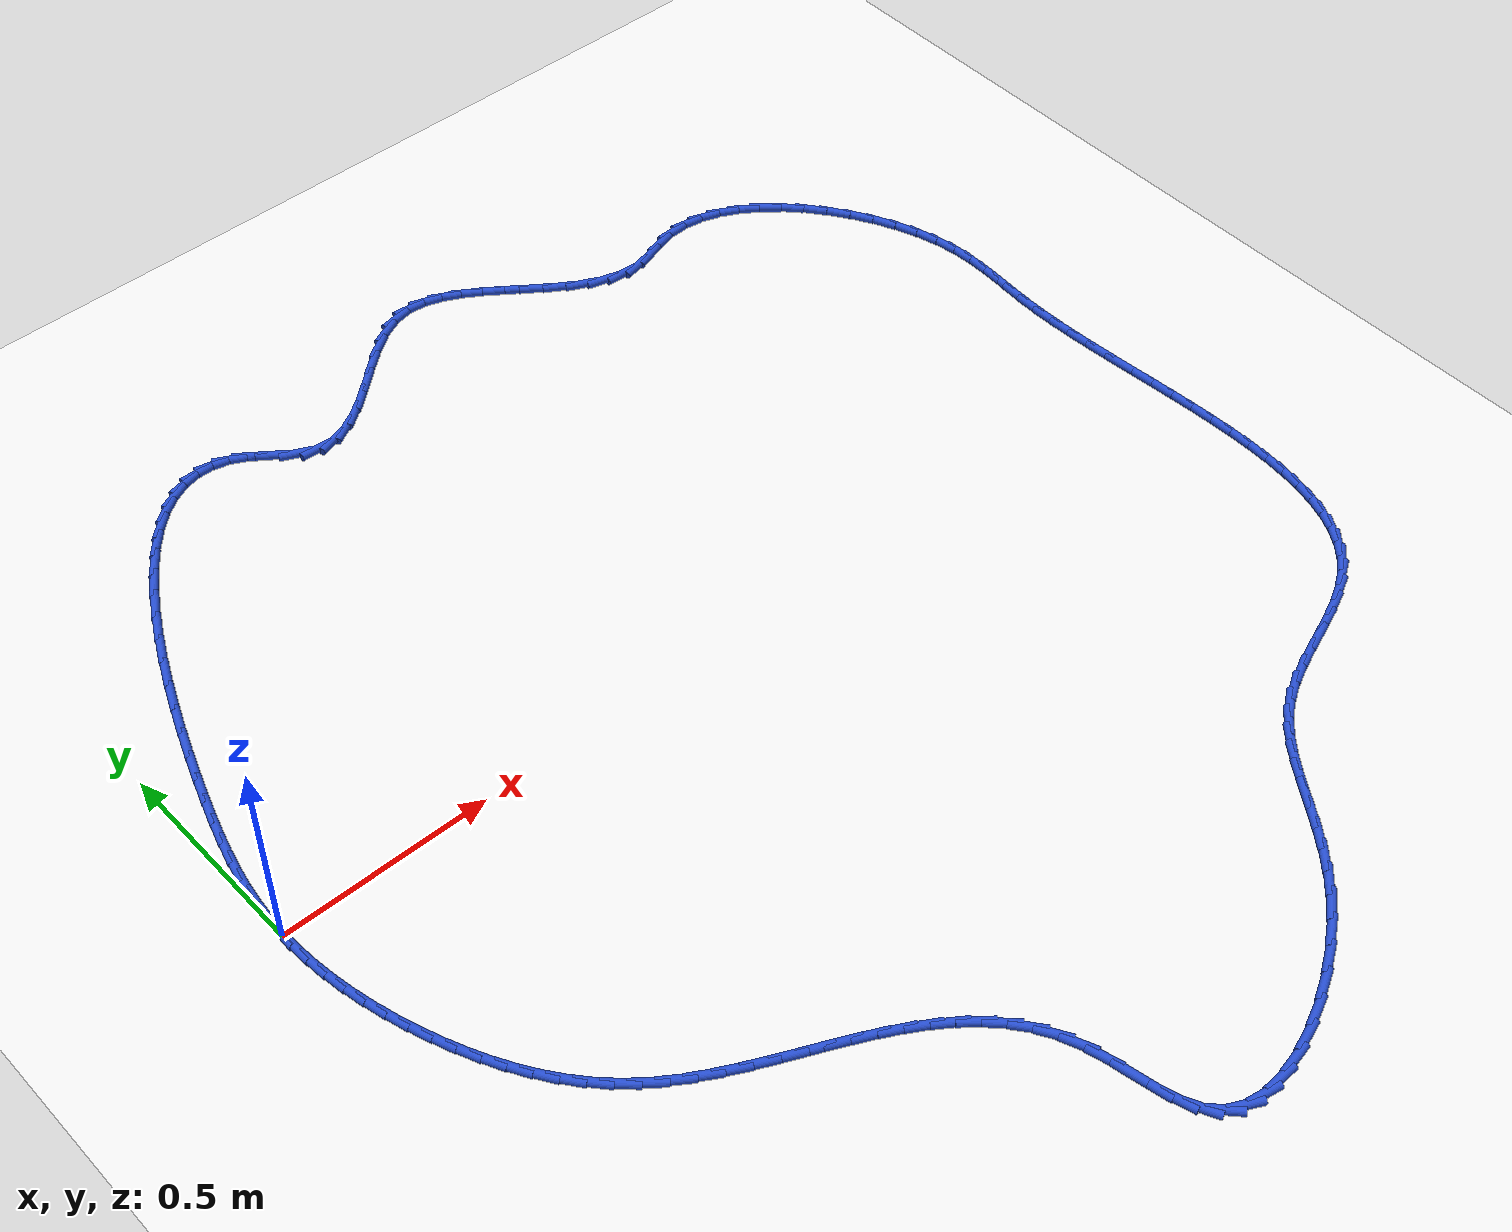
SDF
<sdf version="1.6">
 <world name="default">
  <light name="sun" type="directional">
   <pose>0 0 10 0 -0 0</pose>
   <diffuse>0.8 0.8 0.8 1</diffuse>
   <specular>0.2 0.2 0.2 1</specular>
   <attenuation>
    <range>1000</range>
    <constant>0.9</constant>
    <linear>0.01</linear>
    <quadratic>0.001</quadratic>
   </attenuation>
   <direction>-0.5 0.1 -0.9</direction>
  </light>
  <model name="ground_plane">
   <static>1</static>
   <link name="link">
    <collision name="collision">
     <geometry><plane><normal>0 0 1</normal><size>100 100</size></plane></geometry>
     <surface><friction><ode><mu>100</mu><mu2>50</mu2></ode></friction></surface>
    </collision>
    <visual name="visual">
     <cast_shadows>0</cast_shadows>
     <geometry><plane><normal>0 0 1</normal><size>100 100</size></plane></geometry>
     <material>
      <script><uri>file://media/materials/scripts/gazebo.material</uri><name>Gazebo/WhiteGlow</name></script>
     </material>
    </visual>
   </link>
  </model>
  <gravity>0 0 -9.8</gravity>
  <magnetic_field>6e-06 2.3e-05 -4.2e-05</magnetic_field>
  <atmosphere type="adiabatic"/>
  <physics name="default_physics" default="0" type="ode">
   <max_step_size>0.001</max_step_size>
   <real_time_factor>1</real_time_factor>
   <real_time_update_rate>1000</real_time_update_rate>
  </physics>
  <scene><ambient>0.4 0.4 0.4 1</ambient><background>0.7 0.7 0.7 1</background><shadows>1</shadows></scene>
  <spherical_coordinates>
   <surface_model>EARTH_WGS84</surface_model>
   <latitude_deg>0</latitude_deg>
   <longitude_deg>0</longitude_deg>
   <elevation>0</elevation>
   <heading_deg>0</heading_deg>
  </spherical_coordinates>
  <model name="line">
   <link name="link_0">
    <pose>-6.938893903907228e-18 2.0816681711721685e-17 0.01 0 1.57 1.540561443333834</pose>
    <collision name="collision">
     <geometry><cylinder><radius>0.01</radius><length>0.08</length></cylinder></geometry>
    </collision>
    <visual name="visual">
     <material>
      <script><name>Gazebo/Blue</name><uri>file://media/materials/scripts/gazebo.material</uri></script>
     </material>
     <geometry><cylinder><radius>0.01</radius><length>0.08</length></cylinder></geometry>
    </visual>
   </link>
   <link name="link_1">
    <pose>0.0014410302492590553 0.04764665685887658 0.01 0 1.57 1.482696563486707</pose>
    <collision name="collision">
     <geometry><cylinder><radius>0.01</radius><length>0.08</length></cylinder></geometry>
    </collision>
    <visual name="visual">
     <material>
      <script><name>Gazebo/Blue</name><uri>file://media/materials/scripts/gazebo.material</uri></script>
     </material>
     <geometry><cylinder><radius>0.01</radius><length>0.08</length></cylinder></geometry>
    </visual>
   </link>
   <link name="link_2">
    <pose>0.005607147945011203 0.09481288549213578 0.01 0 1.57 1.4283676075916114</pose>
    <collision name="collision">
     <geometry><cylinder><radius>0.01</radius><length>0.08</length></cylinder></geometry>
    </collision>
    <visual name="visual">
     <material>
      <script><name>Gazebo/Blue</name><uri>file://media/materials/scripts/gazebo.material</uri></script>
     </material>
     <geometry><cylinder><radius>0.01</radius><length>0.08</length></cylinder></geometry>
    </visual>
   </link>
   <link name="link_3">
    <pose>0.012379348391943256 0.14203892915551808 0.01 0 1.57 1.3795591928098352</pose>
    <collision name="collision">
     <geometry><cylinder><radius>0.01</radius><length>0.08</length></cylinder></geometry>
    </collision>
    <visual name="visual">
     <material>
      <script><name>Gazebo/Blue</name><uri>file://media/materials/scripts/gazebo.material</uri></script>
     </material>
     <geometry><cylinder><radius>0.01</radius><length>0.08</length></cylinder></geometry>
    </visual>
   </link>
   <link name="link_4">
    <pose>0.021638626894742018 0.1898650311047639 0.01 0 1.57 1.3376584564360243</pose>
    <collision name="collision">
     <geometry><cylinder><radius>0.01</radius><length>0.08</length></cylinder></geometry>
    </collision>
    <visual name="visual">
     <material>
      <script><name>Gazebo/Blue</name><uri>file://media/materials/scripts/gazebo.material</uri></script>
     </material>
     <geometry><cylinder><radius>0.01</radius><length>0.08</length></cylinder></geometry>
    </visual>
   </link>
   <link name="link_5">
    <pose>0.03326597875809431 0.23883143459561357 0.01 0 1.57 1.3033755333176595</pose>
    <collision name="collision">
     <geometry><cylinder><radius>0.01</radius><length>0.08</length></cylinder></geometry>
    </collision>
    <visual name="visual">
     <material>
      <script><name>Gazebo/Blue</name><uri>file://media/materials/scripts/gazebo.material</uri></script>
     </material>
     <geometry><cylinder><radius>0.01</radius><length>0.08</length></cylinder></geometry>
    </visual>
   </link>
   <link name="link_6">
    <pose>0.04714239928668697 0.2894783828838076 0.01 0 1.57 1.2768050414219354</pose>
    <collision name="collision">
     <geometry><cylinder><radius>0.01</radius><length>0.08</length></cylinder></geometry>
    </collision>
    <visual name="visual">
     <material>
      <script><name>Gazebo/Blue</name><uri>file://media/materials/scripts/gazebo.material</uri></script>
     </material>
     <geometry><cylinder><radius>0.01</radius><length>0.08</length></cylinder></geometry>
    </visual>
   </link>
   <link name="link_7">
    <pose>0.06314888378520678 0.3423461192250864 0.01 0 1.57 1.2575447428191742</pose>
    <collision name="collision">
     <geometry><cylinder><radius>0.01</radius><length>0.08</length></cylinder></geometry>
    </collision>
    <visual name="visual">
     <material>
      <script><name>Gazebo/Blue</name><uri>file://media/materials/scripts/gazebo.material</uri></script>
     </material>
     <geometry><cylinder><radius>0.01</radius><length>0.08</length></cylinder></geometry>
    </visual>
   </link>
   <link name="link_8">
    <pose>0.08116656456038826 0.39797058314323697 0.01 0 1.57 1.2424582086692424</pose>
    <collision name="collision">
     <geometry><cylinder><radius>0.01</radius><length>0.08</length></cylinder></geometry>
    </collision>
    <visual name="visual">
     <material>
      <script><name>Gazebo/Blue</name><uri>file://media/materials/scripts/gazebo.material</uri></script>
     </material>
     <geometry><cylinder><radius>0.01</radius><length>0.08</length></cylinder></geometry>
    </visual>
   </link>
   <link name="link_9">
    <pose>0.10109035269522544 0.4564548727508602 0.01 0 1.57 1.2264654663673669</pose>
    <collision name="collision">
     <geometry><cylinder><radius>0.01</radius><length>0.08</length></cylinder></geometry>
    </collision>
    <visual name="visual">
     <material>
      <script><name>Gazebo/Blue</name><uri>file://media/materials/scripts/gazebo.material</uri></script>
     </material>
     <geometry><cylinder><radius>0.01</radius><length>0.08</length></cylinder></geometry>
    </visual>
   </link>
   <link name="link_10">
    <pose>0.1228405328585811 0.5171050096635283 0.01 0 1.57 1.2086945911875444</pose>
    <collision name="collision">
     <geometry><cylinder><radius>0.01</radius><length>0.08</length></cylinder></geometry>
    </collision>
    <visual name="visual">
     <material>
      <script><name>Gazebo/Blue</name><uri>file://media/materials/scripts/gazebo.material</uri></script>
     </material>
     <geometry><cylinder><radius>0.01</radius><length>0.08</length></cylinder></geometry>
    </visual>
   </link>
   <link name="link_11">
    <pose>0.1463401203233068 0.579141237307107 0.01 0 1.57 1.1887085569846636</pose>
    <collision name="collision">
     <geometry><cylinder><radius>0.01</radius><length>0.08</length></cylinder></geometry>
    </collision>
    <visual name="visual">
     <material>
      <script><name>Gazebo/Blue</name><uri>file://media/materials/scripts/gazebo.material</uri></script>
     </material>
     <geometry><cylinder><radius>0.01</radius><length>0.08</length></cylinder></geometry>
    </visual>
   </link>
   <link name="link_12">
    <pose>0.1715121303622541 0.6417837991074622 0.01 0 1.57 1.1659727087466365</pose>
    <collision name="collision">
     <geometry><cylinder><radius>0.01</radius><length>0.08</length></cylinder></geometry>
    </collision>
    <visual name="visual">
     <material>
      <script><name>Gazebo/Blue</name><uri>file://media/materials/scripts/gazebo.material</uri></script>
     </material>
     <geometry><cylinder><radius>0.01</radius><length>0.08</length></cylinder></geometry>
    </visual>
   </link>
   <link name="link_13">
    <pose>0.19827957824827447 0.704252938490459 0.01 0 1.57 1.1398110968998685</pose>
    <collision name="collision">
     <geometry><cylinder><radius>0.01</radius><length>0.08</length></cylinder></geometry>
    </collision>
    <visual name="visual">
     <material>
      <script><name>Gazebo/Blue</name><uri>file://media/materials/scripts/gazebo.material</uri></script>
     </material>
     <geometry><cylinder><radius>0.01</radius><length>0.08</length></cylinder></geometry>
    </visual>
   </link>
   <link name="link_14">
    <pose>0.22656547925421966 0.7657688988819639 0.01 0 1.57 1.1093476459277243</pose>
    <collision name="collision">
     <geometry><cylinder><radius>0.01</radius><length>0.08</length></cylinder></geometry>
    </collision>
    <visual name="visual">
     <material>
      <script><name>Gazebo/Blue</name><uri>file://media/materials/scripts/gazebo.material</uri></script>
     </material>
     <geometry><cylinder><radius>0.01</radius><length>0.08</length></cylinder></geometry>
    </visual>
   </link>
   <link name="link_15">
    <pose>0.25629284865294105 0.8255519237078421 0.01 0 1.57 1.0734233484225637</pose>
    <collision name="collision">
     <geometry><cylinder><radius>0.01</radius><length>0.08</length></cylinder></geometry>
    </collision>
    <visual name="visual">
     <material>
      <script><name>Gazebo/Blue</name><uri>file://media/materials/scripts/gazebo.material</uri></script>
     </material>
     <geometry><cylinder><radius>0.01</radius><length>0.08</length></cylinder></geometry>
    </visual>
   </link>
   <link name="link_16">
    <pose>0.2873847017172904 0.8828222563939598 0.01 0 1.57 1.0304773418939368</pose>
    <collision name="collision">
     <geometry><cylinder><radius>0.01</radius><length>0.08</length></cylinder></geometry>
    </collision>
    <visual name="visual">
     <material>
      <script><name>Gazebo/Blue</name><uri>file://media/materials/scripts/gazebo.material</uri></script>
     </material>
     <geometry><cylinder><radius>0.01</radius><length>0.08</length></cylinder></geometry>
    </visual>
   </link>
   <link name="link_17">
    <pose>0.3197640537201191 0.9368001403661822 0.01 0 1.57 0.9783757918671593</pose>
    <collision name="collision">
     <geometry><cylinder><radius>0.01</radius><length>0.08</length></cylinder></geometry>
    </collision>
    <visual name="visual">
     <material>
      <script><name>Gazebo/Blue</name><uri>file://media/materials/scripts/gazebo.material</uri></script>
     </material>
     <geometry><cylinder><radius>0.01</radius><length>0.08</length></cylinder></geometry>
    </visual>
   </link>
   <link name="link_18">
    <pose>0.35335391993427884 0.9867058190503755 0.01 0 1.57 0.9141713987903168</pose>
    <collision name="collision">
     <geometry><cylinder><radius>0.01</radius><length>0.08</length></cylinder></geometry>
    </collision>
    <visual name="visual">
     <material>
      <script><name>Gazebo/Blue</name><uri>file://media/materials/scripts/gazebo.material</uri></script>
     </material>
     <geometry><cylinder><radius>0.01</radius><length>0.08</length></cylinder></geometry>
    </visual>
   </link>
   <link name="link_19">
    <pose>0.3880773156326211 1.031759535872405 0.01 0 1.57 0.8337907248591343</pose>
    <collision name="collision">
     <geometry><cylinder><radius>0.01</radius><length>0.08</length></cylinder></geometry>
    </collision>
    <visual name="visual">
     <material>
      <script><name>Gazebo/Blue</name><uri>file://media/materials/scripts/gazebo.material</uri></script>
     </material>
     <geometry><cylinder><radius>0.01</radius><length>0.08</length></cylinder></geometry>
    </visual>
   </link>
   <link name="link_20">
    <pose>0.4238572560879973 1.0711815342581363 0.01 0 1.57 0.7317164382991661</pose>
    <collision name="collision">
     <geometry><cylinder><radius>0.01</radius><length>0.08</length></cylinder></geometry>
    </collision>
    <visual name="visual">
     <material>
      <script><name>Gazebo/Blue</name><uri>file://media/materials/scripts/gazebo.material</uri></script>
     </material>
     <geometry><cylinder><radius>0.01</radius><length>0.08</length></cylinder></geometry>
    </visual>
   </link>
   <link name="link_21">
    <pose>0.4606167565732594 1.104192057633436 0.01 0 1.57 0.6009630091748297</pose>
    <collision name="collision">
     <geometry><cylinder><radius>0.01</radius><length>0.08</length></cylinder></geometry>
    </collision>
    <visual name="visual">
     <material>
      <script><name>Gazebo/Blue</name><uri>file://media/materials/scripts/gazebo.material</uri></script>
     </material>
     <geometry><cylinder><radius>0.01</radius><length>0.08</length></cylinder></geometry>
    </visual>
   </link>
   <link name="link_22">
    <pose>0.4982788323612588 1.1300113494241695 0.01 0 1.57 0.43422189203036354</pose>
    <collision name="collision">
     <geometry><cylinder><radius>0.01</radius><length>0.08</length></cylinder></geometry>
    </collision>
    <visual name="visual">
     <material>
      <script><name>Gazebo/Blue</name><uri>file://media/materials/scripts/gazebo.material</uri></script>
     </material>
     <geometry><cylinder><radius>0.01</radius><length>0.08</length></cylinder></geometry>
    </visual>
   </link>
   <link name="link_23">
    <pose>0.5367664987248468 1.147859653056202 0.01 0 1.57 0.2278399461308863</pose>
    <collision name="collision">
     <geometry><cylinder><radius>0.01</radius><length>0.08</length></cylinder></geometry>
    </collision>
    <visual name="visual">
     <material>
      <script><name>Gazebo/Blue</name><uri>file://media/materials/scripts/gazebo.material</uri></script>
     </material>
     <geometry><cylinder><radius>0.01</radius><length>0.08</length></cylinder></geometry>
    </visual>
   </link>
   <link name="link_24">
    <pose>0.5760027709368756 1.1569572119553997 0.01 0 1.57 -0.010848115206276213</pose>
    <collision name="collision">
     <geometry><cylinder><radius>0.01</radius><length>0.08</length></cylinder></geometry>
    </collision>
    <visual name="visual">
     <material>
      <script><name>Gazebo/Blue</name><uri>file://media/materials/scripts/gazebo.material</uri></script>
     </material>
     <geometry><cylinder><radius>0.01</radius><length>0.08</length></cylinder></geometry>
    </visual>
   </link>
   <link name="link_25">
    <pose>0.6159106642701957 1.1565242695476279 0.01 0 1.57 -0.25927710377033897</pose>
    <collision name="collision">
     <geometry><cylinder><radius>0.01</radius><length>0.08</length></cylinder></geometry>
    </collision>
    <visual name="visual">
     <material>
      <script><name>Gazebo/Blue</name><uri>file://media/materials/scripts/gazebo.material</uri></script>
     </material>
     <geometry><cylinder><radius>0.01</radius><length>0.08</length></cylinder></geometry>
    </visual>
   </link>
   <link name="link_26">
    <pose>0.6564131939976598 1.1457810692587531 0.01 0 1.57 -0.4890548217886547</pose>
    <collision name="collision">
     <geometry><cylinder><radius>0.01</radius><length>0.08</length></cylinder></geometry>
    </collision>
    <visual name="visual">
     <material>
      <script><name>Gazebo/Blue</name><uri>file://media/materials/scripts/gazebo.material</uri></script>
     </material>
     <geometry><cylinder><radius>0.01</radius><length>0.08</length></cylinder></geometry>
    </visual>
   </link>
   <link name="link_27">
    <pose>0.6974333999550183 1.1239511545310417 0.01 0 1.57 -0.6419653435030096</pose>
    <collision name="collision">
     <geometry><cylinder><radius>0.01</radius><length>0.08</length></cylinder></geometry>
    </collision>
    <visual name="visual">
     <material>
      <script><name>Gazebo/Blue</name><uri>file://media/materials/scripts/gazebo.material</uri></script>
     </material>
     <geometry><cylinder><radius>0.01</radius><length>0.08</length></cylinder></geometry>
    </visual>
   </link>
   <link name="link_28">
    <pose>0.7389142836813183 1.092939916203494 0.01 0 1.57 -0.6328869203328106</pose>
    <collision name="collision">
     <geometry><cylinder><radius>0.01</radius><length>0.08</length></cylinder></geometry>
    </collision>
    <visual name="visual">
     <material>
      <script><name>Gazebo/Blue</name><uri>file://media/materials/scripts/gazebo.material</uri></script>
     </material>
     <geometry><cylinder><radius>0.01</radius><length>0.08</length></cylinder></geometry>
    </visual>
   </link>
   <link name="link_29">
    <pose>0.7808548339258498 1.0621746059414716 0.01 0 1.57 -0.43688544674065666</pose>
    <collision name="collision">
     <geometry><cylinder><radius>0.01</radius><length>0.08</length></cylinder></geometry>
    </collision>
    <visual name="visual">
     <material>
      <script><name>Gazebo/Blue</name><uri>file://media/materials/scripts/gazebo.material</uri></script>
     </material>
     <geometry><cylinder><radius>0.01</radius><length>0.08</length></cylinder></geometry>
    </visual>
   </link>
   <link name="link_30">
    <pose>0.8232637040183024 1.0423704591702587 0.01 0 1.57 -0.05161646363902077</pose>
    <collision name="collision">
     <geometry><cylinder><radius>0.01</radius><length>0.08</length></cylinder></geometry>
    </collision>
    <visual name="visual">
     <material>
      <script><name>Gazebo/Blue</name><uri>file://media/materials/scripts/gazebo.material</uri></script>
     </material>
     <geometry><cylinder><radius>0.01</radius><length>0.08</length></cylinder></geometry>
    </visual>
   </link>
   <link name="link_31">
    <pose>0.8661343619887623 1.0401556601295012 0.01 0 1.57 0.29264150111232223</pose>
    <collision name="collision">
     <geometry><cylinder><radius>0.01</radius><length>0.08</length></cylinder></geometry>
    </collision>
    <visual name="visual">
     <material>
      <script><name>Gazebo/Blue</name><uri>file://media/materials/scripts/gazebo.material</uri></script>
     </material>
     <geometry><cylinder><radius>0.01</radius><length>0.08</length></cylinder></geometry>
    </visual>
   </link>
   <link name="link_32">
    <pose>0.9094269889338671 1.0531993731935831 0.01 0 1.57 0.5161902902812335</pose>
    <collision name="collision">
     <geometry><cylinder><radius>0.01</radius><length>0.08</length></cylinder></geometry>
    </collision>
    <visual name="visual">
     <material>
      <script><name>Gazebo/Blue</name><uri>file://media/materials/scripts/gazebo.material</uri></script>
     </material>
     <geometry><cylinder><radius>0.01</radius><length>0.08</length></cylinder></geometry>
    </visual>
   </link>
   <link name="link_33">
    <pose>0.9530973525752291 1.077982923833143 0.01 0 1.57 0.6435274716453541</pose>
    <collision name="collision">
     <geometry><cylinder><radius>0.01</radius><length>0.08</length></cylinder></geometry>
    </collision>
    <visual name="visual">
     <material>
      <script><name>Gazebo/Blue</name><uri>file://media/materials/scripts/gazebo.material</uri></script>
     </material>
     <geometry><cylinder><radius>0.01</radius><length>0.08</length></cylinder></geometry>
    </visual>
   </link>
   <link name="link_34">
    <pose>0.9971012206344609 1.11098763751882 0.01 0 1.57 0.7052542133454133</pose>
    <collision name="collision">
     <geometry><cylinder><radius>0.01</radius><length>0.08</length></cylinder></geometry>
    </collision>
    <visual name="visual">
     <material>
      <script><name>Gazebo/Blue</name><uri>file://media/materials/scripts/gazebo.material</uri></script>
     </material>
     <geometry><cylinder><radius>0.01</radius><length>0.08</length></cylinder></geometry>
    </visual>
   </link>
   <link name="link_35">
    <pose>1.041394360833174 1.1486948397212509 0.01 0 1.57 0.717813154101936</pose>
    <collision name="collision">
     <geometry><cylinder><radius>0.01</radius><length>0.08</length></cylinder></geometry>
    </collision>
    <visual name="visual">
     <material>
      <script><name>Gazebo/Blue</name><uri>file://media/materials/scripts/gazebo.material</uri></script>
     </material>
     <geometry><cylinder><radius>0.01</radius><length>0.08</length></cylinder></geometry>
    </visual>
   </link>
   <link name="link_36">
    <pose>1.085932540892981 1.1875858559110752 0.01 0 1.57 0.6850801937311799</pose>
    <collision name="collision">
     <geometry><cylinder><radius>0.01</radius><length>0.08</length></cylinder></geometry>
    </collision>
    <visual name="visual">
     <material>
      <script><name>Gazebo/Blue</name><uri>file://media/materials/scripts/gazebo.material</uri></script>
     </material>
     <geometry><cylinder><radius>0.01</radius><length>0.08</length></cylinder></geometry>
    </visual>
   </link>
   <link name="link_37">
    <pose>1.1306715285354934 1.224142011558931 0.01 0 1.57 0.5998165933045204</pose>
    <collision name="collision">
     <geometry><cylinder><radius>0.01</radius><length>0.08</length></cylinder></geometry>
    </collision>
    <visual name="visual">
     <material>
      <script><name>Gazebo/Blue</name><uri>file://media/materials/scripts/gazebo.material</uri></script>
     </material>
     <geometry><cylinder><radius>0.01</radius><length>0.08</length></cylinder></geometry>
    </visual>
   </link>
   <link name="link_38">
    <pose>1.175567091482324 1.2548446321354563 0.01 0 1.57 0.4425715776363919</pose>
    <collision name="collision">
     <geometry><cylinder><radius>0.01</radius><length>0.08</length></cylinder></geometry>
    </collision>
    <visual name="visual">
     <material>
      <script><name>Gazebo/Blue</name><uri>file://media/materials/scripts/gazebo.material</uri></script>
     </material>
     <geometry><cylinder><radius>0.01</radius><length>0.08</length></cylinder></geometry>
    </visual>
   </link>
   <link name="link_39">
    <pose>1.2205749974550848 1.2761750431112902 0.01 0 1.57 0.18781690993796982</pose>
    <collision name="collision">
     <geometry><cylinder><radius>0.01</radius><length>0.08</length></cylinder></geometry>
    </collision>
    <visual name="visual">
     <material>
      <script><name>Gazebo/Blue</name><uri>file://media/materials/scripts/gazebo.material</uri></script>
     </material>
     <geometry><cylinder><radius>0.01</radius><length>0.08</length></cylinder></geometry>
    </visual>
   </link>
   <link name="link_40">
    <pose>1.265652699115217 1.2847423735206294 0.01 0 1.57 -0.10372344730545793</pose>
    <collision name="collision">
     <geometry><cylinder><radius>0.01</radius><length>0.08</length></cylinder></geometry>
    </collision>
    <visual name="visual">
     <material>
      <script><name>Gazebo/Blue</name><uri>file://media/materials/scripts/gazebo.material</uri></script>
     </material>
     <geometry><cylinder><radius>0.01</radius><length>0.08</length></cylinder></geometry>
    </visual>
   </link>
   <link name="link_41">
    <pose>1.3107957156700965 1.2800431197311006 0.01 0 1.57 -0.33225902819154934</pose>
    <collision name="collision">
     <geometry><cylinder><radius>0.01</radius><length>0.08</length></cylinder></geometry>
    </collision>
    <visual name="visual">
     <material>
      <script><name>Gazebo/Blue</name><uri>file://media/materials/scripts/gazebo.material</uri></script>
     </material>
     <geometry><cylinder><radius>0.01</radius><length>0.08</length></cylinder></geometry>
    </visual>
   </link>
   <link name="link_42">
    <pose>1.3560372550352864 1.2644324862540475 0.01 0 1.57 -0.48729063209119505</pose>
    <collision name="collision">
     <geometry><cylinder><radius>0.01</radius><length>0.08</length></cylinder></geometry>
    </collision>
    <visual name="visual">
     <material>
      <script><name>Gazebo/Blue</name><uri>file://media/materials/scripts/gazebo.material</uri></script>
     </material>
     <geometry><cylinder><radius>0.01</radius><length>0.08</length></cylinder></geometry>
    </visual>
   </link>
   <link name="link_43">
    <pose>1.4014121344962753 1.2403877491476336 0.01 0 1.57 -0.582503155691921</pose>
    <collision name="collision">
     <geometry><cylinder><radius>0.01</radius><length>0.08</length></cylinder></geometry>
    </collision>
    <visual name="visual">
     <material>
      <script><name>Gazebo/Blue</name><uri>file://media/materials/scripts/gazebo.material</uri></script>
     </material>
     <geometry><cylinder><radius>0.01</radius><length>0.08</length></cylinder></geometry>
    </visual>
   </link>
   <link name="link_44">
    <pose>1.446955171338551 1.2103861844700214 0.01 0 1.57 -0.6318105705020849</pose>
    <collision name="collision">
     <geometry><cylinder><radius>0.01</radius><length>0.08</length></cylinder></geometry>
    </collision>
    <visual name="visual">
     <material>
      <script><name>Gazebo/Blue</name><uri>file://media/materials/scripts/gazebo.material</uri></script>
     </material>
     <geometry><cylinder><radius>0.01</radius><length>0.08</length></cylinder></geometry>
    </visual>
   </link>
   <link name="link_45">
    <pose>1.4927011828475996 1.1769050682793745 0.01 0 1.57 -0.6434390186435228</pose>
    <collision name="collision">
     <geometry><cylinder><radius>0.01</radius><length>0.08</length></cylinder></geometry>
    </collision>
    <visual name="visual">
     <material>
      <script><name>Gazebo/Blue</name><uri>file://media/materials/scripts/gazebo.material</uri></script>
     </material>
     <geometry><cylinder><radius>0.01</radius><length>0.08</length></cylinder></geometry>
    </visual>
   </link>
   <link name="link_46">
    <pose>1.5386849863089096 1.1424216766338549 0.01 0 1.57 -0.6197926337899876</pose>
    <collision name="collision">
     <geometry><cylinder><radius>0.01</radius><length>0.08</length></cylinder></geometry>
    </collision>
    <visual name="visual">
     <material>
      <script><name>Gazebo/Blue</name><uri>file://media/materials/scripts/gazebo.material</uri></script>
     </material>
     <geometry><cylinder><radius>0.01</radius><length>0.08</length></cylinder></geometry>
    </visual>
   </link>
   <link name="link_47">
    <pose>1.5849413990079688 1.1094132855916274 0.01 0 1.57 -0.5578841990169563</pose>
    <collision name="collision">
     <geometry><cylinder><radius>0.01</radius><length>0.08</length></cylinder></geometry>
    </collision>
    <visual name="visual">
     <material>
      <script><name>Gazebo/Blue</name><uri>file://media/materials/scripts/gazebo.material</uri></script>
     </material>
     <geometry><cylinder><radius>0.01</radius><length>0.08</length></cylinder></geometry>
    </visual>
   </link>
   <link name="link_48">
    <pose>1.6315052382302642 1.0803571712108535 0.01 0 1.57 -0.4494526008905176</pose>
    <collision name="collision">
     <geometry><cylinder><radius>0.01</radius><length>0.08</length></cylinder></geometry>
    </collision>
    <visual name="visual">
     <material>
      <script><name>Gazebo/Blue</name><uri>file://media/materials/scripts/gazebo.material</uri></script>
     </material>
     <geometry><cylinder><radius>0.01</radius><length>0.08</length></cylinder></geometry>
    </visual>
   </link>
   <link name="link_49">
    <pose>1.678411321261283 1.0577306095496972 0.01 0 1.57 -0.28240609169446207</pose>
    <collision name="collision">
     <geometry><cylinder><radius>0.01</radius><length>0.08</length></cylinder></geometry>
    </collision>
    <visual name="visual">
     <material>
      <script><name>Gazebo/Blue</name><uri>file://media/materials/scripts/gazebo.material</uri></script>
     </material>
     <geometry><cylinder><radius>0.01</radius><length>0.08</length></cylinder></geometry>
    </visual>
   </link>
   <link name="link_50">
    <pose>1.7256944653865132 1.0440108766663214 0.01 0 1.57 -0.04893097034756909</pose>
    <collision name="collision">
     <geometry><cylinder><radius>0.01</radius><length>0.08</length></cylinder></geometry>
    </collision>
    <visual name="visual">
     <material>
      <script><name>Gazebo/Blue</name><uri>file://media/materials/scripts/gazebo.material</uri></script>
     </material>
     <geometry><cylinder><radius>0.01</radius><length>0.08</length></cylinder></geometry>
    </visual>
   </link>
   <link name="link_51">
    <pose>1.7733894878914425 1.0416752486188887 0.01 0 1.57 0.21309796185872423</pose>
    <collision name="collision">
     <geometry><cylinder><radius>0.01</radius><length>0.08</length></cylinder></geometry>
    </collision>
    <visual name="visual">
     <material>
      <script><name>Gazebo/Blue</name><uri>file://media/materials/scripts/gazebo.material</uri></script>
     </material>
     <geometry><cylinder><radius>0.01</radius><length>0.08</length></cylinder></geometry>
    </visual>
   </link>
   <link name="link_52">
    <pose>1.8215212440681692 1.052090156665066 0.01 0 1.57 0.3240529821937707</pose>
    <collision name="collision">
     <geometry><cylinder><radius>0.01</radius><length>0.08</length></cylinder></geometry>
    </collision>
    <visual name="visual">
     <material>
      <script><name>Gazebo/Blue</name><uri>file://media/materials/scripts/gazebo.material</uri></script>
     </material>
     <geometry><cylinder><radius>0.01</radius><length>0.08</length></cylinder></geometry>
    </visual>
   </link>
   <link name="link_53">
    <pose>1.8700407427818067 1.0683875436172379 0.01 0 1.57 0.23576746180758953</pose>
    <collision name="collision">
     <geometry><cylinder><radius>0.01</radius><length>0.08</length></cylinder></geometry>
    </collision>
    <visual name="visual">
     <material>
      <script><name>Gazebo/Blue</name><uri>file://media/materials/scripts/gazebo.material</uri></script>
     </material>
     <geometry><cylinder><radius>0.01</radius><length>0.08</length></cylinder></geometry>
    </visual>
   </link>
   <link name="link_54">
    <pose>1.9188618709374892 1.0801161024042396 0.01 0 1.57 0.029143896271335196</pose>
    <collision name="collision">
     <geometry><cylinder><radius>0.01</radius><length>0.08</length></cylinder></geometry>
    </collision>
    <visual name="visual">
     <material>
      <script><name>Gazebo/Blue</name><uri>file://media/materials/scripts/gazebo.material</uri></script>
     </material>
     <geometry><cylinder><radius>0.01</radius><length>0.08</length></cylinder></geometry>
    </visual>
   </link>
   <link name="link_55">
    <pose>1.9677392440365904 1.0815409829340532 0.01 0 1.57 -0.17071934907159508</pose>
    <collision name="collision">
     <geometry><cylinder><radius>0.01</radius><length>0.08</length></cylinder></geometry>
    </collision>
    <visual name="visual">
     <material>
      <script><name>Gazebo/Blue</name><uri>file://media/materials/scripts/gazebo.material</uri></script>
     </material>
     <geometry><cylinder><radius>0.01</radius><length>0.08</length></cylinder></geometry>
    </visual>
   </link>
   <link name="link_56">
    <pose>2.0162172087202537 1.0731835049948966 0.01 0 1.57 -0.34649386268864046</pose>
    <collision name="collision">
     <geometry><cylinder><radius>0.01</radius><length>0.08</length></cylinder></geometry>
    </collision>
    <visual name="visual">
     <material>
      <script><name>Gazebo/Blue</name><uri>file://media/materials/scripts/gazebo.material</uri></script>
     </material>
     <geometry><cylinder><radius>0.01</radius><length>0.08</length></cylinder></geometry>
    </visual>
   </link>
   <link name="link_57">
    <pose>2.0638256934931287 1.0559939739658677 0.01 0 1.57 -0.49657212601732936</pose>
    <collision name="collision">
     <geometry><cylinder><radius>0.01</radius><length>0.08</length></cylinder></geometry>
    </collision>
    <visual name="visual">
     <material>
      <script><name>Gazebo/Blue</name><uri>file://media/materials/scripts/gazebo.material</uri></script>
     </material>
     <geometry><cylinder><radius>0.01</radius><length>0.08</length></cylinder></geometry>
    </visual>
   </link>
   <link name="link_58">
    <pose>2.1100946268598677 1.030922695226064 0.01 0 1.57 -0.6239047964831007</pose>
    <collision name="collision">
     <geometry><cylinder><radius>0.01</radius><length>0.08</length></cylinder></geometry>
    </collision>
    <visual name="visual">
     <material>
      <script><name>Gazebo/Blue</name><uri>file://media/materials/scripts/gazebo.material</uri></script>
     </material>
     <geometry><cylinder><radius>0.01</radius><length>0.08</length></cylinder></geometry>
    </visual>
   </link>
   <link name="link_59">
    <pose>2.1545539373251206 0.9989199741545837 0.01 0 1.57 -0.7331058571873689</pose>
    <collision name="collision">
     <geometry><cylinder><radius>0.01</radius><length>0.08</length></cylinder></geometry>
    </collision>
    <visual name="visual">
     <material>
      <script><name>Gazebo/Blue</name><uri>file://media/materials/scripts/gazebo.material</uri></script>
     </material>
     <geometry><cylinder><radius>0.01</radius><length>0.08</length></cylinder></geometry>
    </visual>
   </link>
   <link name="link_60">
    <pose>2.1967335533935386 0.9609361161305241 0.01 0 1.57 -0.828852620681469</pose>
    <collision name="collision">
     <geometry><cylinder><radius>0.01</radius><length>0.08</length></cylinder></geometry>
    </collision>
    <visual name="visual">
     <material>
      <script><name>Gazebo/Blue</name><uri>file://media/materials/scripts/gazebo.material</uri></script>
     </material>
     <geometry><cylinder><radius>0.01</radius><length>0.08</length></cylinder></geometry>
    </visual>
   </link>
   <link name="link_61">
    <pose>2.236163403569772 0.9179214265329823 0.01 0 1.57 -0.9153285390216788</pose>
    <collision name="collision">
     <geometry><cylinder><radius>0.01</radius><length>0.08</length></cylinder></geometry>
    </collision>
    <visual name="visual">
     <material>
      <script><name>Gazebo/Blue</name><uri>file://media/materials/scripts/gazebo.material</uri></script>
     </material>
     <geometry><cylinder><radius>0.01</radius><length>0.08</length></cylinder></geometry>
    </visual>
   </link>
   <link name="link_62">
    <pose>2.2723734163584717 0.8708262107410567 0.01 0 1.57 -0.9961927366485599</pose>
    <collision name="collision">
     <geometry><cylinder><radius>0.01</radius><length>0.08</length></cylinder></geometry>
    </collision>
    <visual name="visual">
     <material>
      <script><name>Gazebo/Blue</name><uri>file://media/materials/scripts/gazebo.material</uri></script>
     </material>
     <geometry><cylinder><radius>0.01</radius><length>0.08</length></cylinder></geometry>
    </visual>
   </link>
   <link name="link_63">
    <pose>2.3048935202642897 0.8206007741338441 0.01 0 1.57 -1.0747588463839106</pose>
    <collision name="collision">
     <geometry><cylinder><radius>0.01</radius><length>0.08</length></cylinder></geometry>
    </collision>
    <visual name="visual">
     <material>
      <script><name>Gazebo/Blue</name><uri>file://media/materials/scripts/gazebo.material</uri></script>
     </material>
     <geometry><cylinder><radius>0.01</radius><length>0.08</length></cylinder></geometry>
    </visual>
   </link>
   <link name="link_64">
    <pose>2.3332536437918754 0.7681954220904431 0.01 0 1.57 -1.1542498780535932</pose>
    <collision name="collision">
     <geometry><cylinder><radius>0.01</radius><length>0.08</length></cylinder></geometry>
    </collision>
    <visual name="visual">
     <material>
      <script><name>Gazebo/Blue</name><uri>file://media/materials/scripts/gazebo.material</uri></script>
     </material>
     <geometry><cylinder><radius>0.01</radius><length>0.08</length></cylinder></geometry>
    </visual>
   </link>
   <link name="link_65">
    <pose>2.3569837154458795 0.7145604599899507 0.01 0 1.57 -1.2380934578223823</pose>
    <collision name="collision">
     <geometry><cylinder><radius>0.01</radius><length>0.08</length></cylinder></geometry>
    </collision>
    <visual name="visual">
     <material>
      <script><name>Gazebo/Blue</name><uri>file://media/materials/scripts/gazebo.material</uri></script>
     </material>
     <geometry><cylinder><radius>0.01</radius><length>0.08</length></cylinder></geometry>
    </visual>
   </link>
   <link name="link_66">
    <pose>2.3756136637309546 0.6606461932114642 0.01 0 1.57 -1.3302605839326542</pose>
    <collision name="collision">
     <geometry><cylinder><radius>0.01</radius><length>0.08</length></cylinder></geometry>
    </collision>
    <visual name="visual">
     <material>
      <script><name>Gazebo/Blue</name><uri>file://media/materials/scripts/gazebo.material</uri></script>
     </material>
     <geometry><cylinder><radius>0.01</radius><length>0.08</length></cylinder></geometry>
    </visual>
   </link>
   <link name="link_67">
    <pose>2.3886734171517503 0.6074029271340823 0.01 0 1.57 -1.4332412111913022</pose>
    <collision name="collision">
     <geometry><cylinder><radius>0.01</radius><length>0.08</length></cylinder></geometry>
    </collision>
    <visual name="visual">
     <material>
      <script><name>Gazebo/Blue</name><uri>file://media/materials/scripts/gazebo.material</uri></script>
     </material>
     <geometry><cylinder><radius>0.01</radius><length>0.08</length></cylinder></geometry>
    </visual>
   </link>
   <link name="link_68">
    <pose>2.3958355720449203 0.5556642107099964 0.01 0 1.57 -1.5280895810811743</pose>
    <collision name="collision">
     <geometry><cylinder><radius>0.01</radius><length>0.08</length></cylinder></geometry>
    </collision>
    <visual name="visual">
     <material>
      <script><name>Gazebo/Blue</name><uri>file://media/materials/scripts/gazebo.material</uri></script>
     </material>
     <geometry><cylinder><radius>0.01</radius><length>0.08</length></cylinder></geometry>
    </visual>
   </link>
   <link name="link_69">
    <pose>2.397989135031883 0.5052681076688 0.01 0 1.57 1.5436450222899472</pose>
    <collision name="collision">
     <geometry><cylinder><radius>0.01</radius><length>0.08</length></cylinder></geometry>
    </collision>
    <visual name="visual">
     <material>
      <script><name>Gazebo/Blue</name><uri>file://media/materials/scripts/gazebo.material</uri></script>
     </material>
     <geometry><cylinder><radius>0.01</radius><length>0.08</length></cylinder></geometry>
    </visual>
   </link>
   <link name="link_70">
    <pose>2.396638858285217 0.4555487682129303 0.01 0 1.57 1.5036188367684367</pose>
    <collision name="collision">
     <geometry><cylinder><radius>0.01</radius><length>0.08</length></cylinder></geometry>
    </collision>
    <visual name="visual">
     <material>
      <script><name>Gazebo/Blue</name><uri>file://media/materials/scripts/gazebo.material</uri></script>
     </material>
     <geometry><cylinder><radius>0.01</radius><length>0.08</length></cylinder></geometry>
    </visual>
   </link>
   <link name="link_71">
    <pose>2.393294275469465 0.4058364294698929 0.01 0 1.57 1.4949254189355496</pose>
    <collision name="collision">
     <geometry><cylinder><radius>0.01</radius><length>0.08</length></cylinder></geometry>
    </collision>
    <visual name="visual">
     <material>
      <script><name>Gazebo/Blue</name><uri>file://media/materials/scripts/gazebo.material</uri></script>
     </material>
     <geometry><cylinder><radius>0.01</radius><length>0.08</length></cylinder></geometry>
    </visual>
   </link>
   <link name="link_72">
    <pose>2.389464920249171 0.3554613285671945 0.01 0 1.57 1.5165648073472573</pose>
    <collision name="collision">
     <geometry><cylinder><radius>0.01</radius><length>0.08</length></cylinder></geometry>
    </collision>
    <visual name="visual">
     <material>
      <script><name>Gazebo/Blue</name><uri>file://media/materials/scripts/gazebo.material</uri></script>
     </material>
     <geometry><cylinder><radius>0.01</radius><length>0.08</length></cylinder></geometry>
    </visual>
   </link>
   <link name="link_73">
    <pose>2.386658048036832 0.3037548675121264 0.01 0 1.57 1.5558300991698204</pose>
    <collision name="collision">
     <geometry><cylinder><radius>0.01</radius><length>0.08</length></cylinder></geometry>
    </collision>
    <visual name="visual">
     <material>
      <script><name>Gazebo/Blue</name><uri>file://media/materials/scripts/gazebo.material</uri></script>
     </material>
     <geometry><cylinder><radius>0.01</radius><length>0.08</length></cylinder></geometry>
    </visual>
   </link>
   <link name="link_74">
    <pose>2.385858205742414 0.25031571135257835 0.01 0 1.57 -1.5525078734038376</pose>
    <collision name="collision">
     <geometry><cylinder><radius>0.01</radius><length>0.08</length></cylinder></geometry>
    </collision>
    <visual name="visual">
     <material>
      <script><name>Gazebo/Blue</name><uri>file://media/materials/scripts/gazebo.material</uri></script>
     </material>
     <geometry><cylinder><radius>0.01</radius><length>0.08</length></cylinder></geometry>
    </visual>
   </link>
   <link name="link_75">
    <pose>2.386863571770721 0.19534912030835666 0.01 0 1.57 -1.52732123186851</pose>
    <collision name="collision">
     <geometry><cylinder><radius>0.01</radius><length>0.08</length></cylinder></geometry>
    </collision>
    <visual name="visual">
     <material>
      <script><name>Gazebo/Blue</name><uri>file://media/materials/scripts/gazebo.material</uri></script>
     </material>
     <geometry><cylinder><radius>0.01</radius><length>0.08</length></cylinder></geometry>
    </visual>
   </link>
   <link name="link_76">
    <pose>2.38930863315938 0.13914405067901345 0.01 0 1.57 -1.509299845566224</pose>
    <collision name="collision">
     <geometry><cylinder><radius>0.01</radius><length>0.08</length></cylinder></geometry>
    </collision>
    <visual name="visual">
     <material>
      <script><name>Gazebo/Blue</name><uri>file://media/materials/scripts/gazebo.material</uri></script>
     </material>
     <geometry><cylinder><radius>0.01</radius><length>0.08</length></cylinder></geometry>
    </visual>
   </link>
   <link name="link_77">
    <pose>2.392827876946014 0.08198945876410216 0.01 0 1.57 -1.4977981564269176</pose>
    <collision name="collision">
     <geometry><cylinder><radius>0.01</radius><length>0.08</length></cylinder></geometry>
    </collision>
    <visual name="visual">
     <material>
      <script><name>Gazebo/Blue</name><uri>file://media/materials/scripts/gazebo.material</uri></script>
     </material>
     <geometry><cylinder><radius>0.01</radius><length>0.08</length></cylinder></geometry>
    </visual>
   </link>
   <link name="link_78">
    <pose>2.397055790168252 0.024174300863174444 0.01 0 1.57 -1.4923987602151094</pose>
    <collision name="collision">
     <geometry><cylinder><radius>0.01</radius><length>0.08</length></cylinder></geometry>
    </collision>
    <visual name="visual">
     <material>
      <script><name>Gazebo/Blue</name><uri>file://media/materials/scripts/gazebo.material</uri></script>
     </material>
     <geometry><cylinder><radius>0.01</radius><length>0.08</length></cylinder></geometry>
    </visual>
   </link>
   <link name="link_79">
    <pose>2.4016268598637174 -0.034012466724216116 0.01 0 1.57 -1.4928908498108762</pose>
    <collision name="collision">
     <geometry><cylinder><radius>0.01</radius><length>0.08</length></cylinder></geometry>
    </collision>
    <visual name="visual">
     <material>
      <script><name>Gazebo/Blue</name><uri>file://media/materials/scripts/gazebo.material</uri></script>
     </material>
     <geometry><cylinder><radius>0.01</radius><length>0.08</length></cylinder></geometry>
    </visual>
   </link>
   <link name="link_80">
    <pose>2.4061755730700365 -0.09228188769851749 0.01 0 1.57 -1.4992579143648588</pose>
    <collision name="collision">
     <geometry><cylinder><radius>0.01</radius><length>0.08</length></cylinder></geometry>
    </collision>
    <visual name="visual">
     <material>
      <script><name>Gazebo/Blue</name><uri>file://media/materials/scripts/gazebo.material</uri></script>
     </material>
     <geometry><cylinder><radius>0.01</radius><length>0.08</length></cylinder></geometry>
    </visual>
   </link>
   <link name="link_81">
    <pose>2.410336416824834 -0.15034500576017712 0.01 0 1.57 -1.5116749627255117</pose>
    <collision name="collision">
     <geometry><cylinder><radius>0.01</radius><length>0.08</length></cylinder></geometry>
    </collision>
    <visual name="visual">
     <material>
      <script><name>Gazebo/Blue</name><uri>file://media/materials/scripts/gazebo.material</uri></script>
     </material>
     <geometry><cylinder><radius>0.01</radius><length>0.08</length></cylinder></geometry>
    </visual>
   </link>
   <link name="link_82">
    <pose>2.413743878165737 -0.20791286460964334 0.01 0 1.57 -1.5305148673764126</pose>
    <collision name="collision">
     <geometry><cylinder><radius>0.01</radius><length>0.08</length></cylinder></geometry>
    </collision>
    <visual name="visual">
     <material>
      <script><name>Gazebo/Blue</name><uri>file://media/materials/scripts/gazebo.material</uri></script>
     </material>
     <geometry><cylinder><radius>0.01</radius><length>0.08</length></cylinder></geometry>
    </visual>
   </link>
   <link name="link_83">
    <pose>2.4160324441303698 -0.26469650794736166 0.01 0 1.57 -1.556362742582866</pose>
    <collision name="collision">
     <geometry><cylinder><radius>0.01</radius><length>0.08</length></cylinder></geometry>
    </collision>
    <visual name="visual">
     <material>
      <script><name>Gazebo/Blue</name><uri>file://media/materials/scripts/gazebo.material</uri></script>
     </material>
     <geometry><cylinder><radius>0.01</radius><length>0.08</length></cylinder></geometry>
    </visual>
   </link>
   <link name="link_84">
    <pose>2.4168366017563585 -0.32040697947378044 0.01 0 1.57 1.5515568325713953</pose>
    <collision name="collision">
     <geometry><cylinder><radius>0.01</radius><length>0.08</length></cylinder></geometry>
    </collision>
    <visual name="visual">
     <material>
      <script><name>Gazebo/Blue</name><uri>file://media/materials/scripts/gazebo.material</uri></script>
     </material>
     <geometry><cylinder><radius>0.01</radius><length>0.08</length></cylinder></geometry>
    </visual>
   </link>
   <link name="link_85">
    <pose>2.4157908380813287 -0.3747553228893472 0.01 0 1.57 1.5089896166461112</pose>
    <collision name="collision">
     <geometry><cylinder><radius>0.01</radius><length>0.08</length></cylinder></geometry>
    </collision>
    <visual name="visual">
     <material>
      <script><name>Gazebo/Blue</name><uri>file://media/materials/scripts/gazebo.material</uri></script>
     </material>
     <geometry><cylinder><radius>0.01</radius><length>0.08</length></cylinder></geometry>
    </visual>
   </link>
   <link name="link_86">
    <pose>2.412529640142906 -0.4274525818945093 0.01 0 1.57 1.4562008136904623</pose>
    <collision name="collision">
     <geometry><cylinder><radius>0.01</radius><length>0.08</length></cylinder></geometry>
    </collision>
    <visual name="visual">
     <material>
      <script><name>Gazebo/Blue</name><uri>file://media/materials/scripts/gazebo.material</uri></script>
     </material>
     <geometry><cylinder><radius>0.01</radius><length>0.08</length></cylinder></geometry>
    </visual>
   </link>
   <link name="link_87">
    <pose>2.4066874949787156 -0.4782098001897152 0.01 0 1.57 1.3916352321338998</pose>
    <collision name="collision">
     <geometry><cylinder><radius>0.01</radius><length>0.08</length></cylinder></geometry>
    </collision>
    <visual name="visual">
     <material>
      <script><name>Gazebo/Blue</name><uri>file://media/materials/scripts/gazebo.material</uri></script>
     </material>
     <geometry><cylinder><radius>0.01</radius><length>0.08</length></cylinder></geometry>
    </visual>
   </link>
   <link name="link_88">
    <pose>2.3978988896263838 -0.5267380214754103 0.01 0 1.57 1.3136227654888197</pose>
    <collision name="collision">
     <geometry><cylinder><radius>0.01</radius><length>0.08</length></cylinder></geometry>
    </collision>
    <visual name="visual">
     <material>
      <script><name>Gazebo/Blue</name><uri>file://media/materials/scripts/gazebo.material</uri></script>
     </material>
     <geometry><cylinder><radius>0.01</radius><length>0.08</length></cylinder></geometry>
    </visual>
   </link>
   <link name="link_89">
    <pose>2.3857983111235352 -0.572748289452043 0.01 0 1.57 1.2206409488602057</pose>
    <collision name="collision">
     <geometry><cylinder><radius>0.01</radius><length>0.08</length></cylinder></geometry>
    </collision>
    <visual name="visual">
     <material>
      <script><name>Gazebo/Blue</name><uri>file://media/materials/scripts/gazebo.material</uri></script>
     </material>
     <geometry><cylinder><radius>0.01</radius><length>0.08</length></cylinder></geometry>
    </visual>
   </link>
   <link name="link_90">
    <pose>2.370020246507796 -0.6159516478200607 0.01 0 1.57 1.1118006580434525</pose>
    <collision name="collision">
     <geometry><cylinder><radius>0.01</radius><length>0.08</length></cylinder></geometry>
    </collision>
    <visual name="visual">
     <material>
      <script><name>Gazebo/Blue</name><uri>file://media/materials/scripts/gazebo.material</uri></script>
     </material>
     <geometry><cylinder><radius>0.01</radius><length>0.08</length></cylinder></geometry>
    </visual>
   </link>
   <link name="link_91">
    <pose>2.3501991828167923 -0.6560591402799111 0.01 0 1.57 0.9875634459735474</pose>
    <collision name="collision">
     <geometry><cylinder><radius>0.01</radius><length>0.08</length></cylinder></geometry>
    </collision>
    <visual name="visual">
     <material>
      <script><name>Gazebo/Blue</name><uri>file://media/materials/scripts/gazebo.material</uri></script>
     </material>
     <geometry><cylinder><radius>0.01</radius><length>0.08</length></cylinder></geometry>
    </visual>
   </link>
   <link name="link_92">
    <pose>2.3259696070881484 -0.692781810532042 0.01 0 1.57 0.8504974801002713</pose>
    <collision name="collision">
     <geometry><cylinder><radius>0.01</radius><length>0.08</length></cylinder></geometry>
    </collision>
    <visual name="visual">
     <material>
      <script><name>Gazebo/Blue</name><uri>file://media/materials/scripts/gazebo.material</uri></script>
     </material>
     <geometry><cylinder><radius>0.01</radius><length>0.08</length></cylinder></geometry>
    </visual>
   </link>
   <link name="link_93">
    <pose>2.296966006359491 -0.7258307022768995 0.01 0 1.57 0.7055895797726708</pose>
    <collision name="collision">
     <geometry><cylinder><radius>0.01</radius><length>0.08</length></cylinder></geometry>
    </collision>
    <visual name="visual">
     <material>
      <script><name>Gazebo/Blue</name><uri>file://media/materials/scripts/gazebo.material</uri></script>
     </material>
     <geometry><cylinder><radius>0.01</radius><length>0.08</length></cylinder></geometry>
    </visual>
   </link>
   <link name="link_94">
    <pose>2.262822867668445 -0.7549168592149318 0.01 0 1.57 0.5620450698267485</pose>
    <collision name="collision">
     <geometry><cylinder><radius>0.01</radius><length>0.08</length></cylinder></geometry>
    </collision>
    <visual name="visual">
     <material>
      <script><name>Gazebo/Blue</name><uri>file://media/materials/scripts/gazebo.material</uri></script>
     </material>
     <geometry><cylinder><radius>0.01</radius><length>0.08</length></cylinder></geometry>
    </visual>
   </link>
   <link name="link_95">
    <pose>2.2232693308701883 -0.7798277602729524 0.01 0 1.57 0.4503980553552897</pose>
    <collision name="collision">
     <geometry><cylinder><radius>0.01</radius><length>0.08</length></cylinder></geometry>
    </collision>
    <visual name="visual">
     <material>
      <script><name>Gazebo/Blue</name><uri>file://media/materials/scripts/gazebo.material</uri></script>
     </material>
     <geometry><cylinder><radius>0.01</radius><length>0.08</length></cylinder></geometry>
    </visual>
   </link>
   <link name="link_96">
    <pose>2.1790801612072 -0.8011952608605857 0.01 0 1.57 0.3808741684488332</pose>
    <collision name="collision">
     <geometry><cylinder><radius>0.01</radius><length>0.08</length></cylinder></geometry>
    </collision>
    <visual name="visual">
     <material>
      <script><name>Gazebo/Blue</name><uri>file://media/materials/scripts/gazebo.material</uri></script>
     </material>
     <geometry><cylinder><radius>0.01</radius><length>0.08</length></cylinder></geometry>
    </visual>
   </link>
   <link name="link_97">
    <pose>2.1316796180220736 -0.8201757039816925 0.01 0 1.57 0.3465193372691935</pose>
    <collision name="collision">
     <geometry><cylinder><radius>0.01</radius><length>0.08</length></cylinder></geometry>
    </collision>
    <visual name="visual">
     <material>
      <script><name>Gazebo/Blue</name><uri>file://media/materials/scripts/gazebo.material</uri></script>
     </material>
     <geometry><cylinder><radius>0.01</radius><length>0.08</length></cylinder></geometry>
    </visual>
   </link>
   <link name="link_98">
    <pose>2.082501711639624 -0.8379333068751836 0.01 0 1.57 0.3432534417044903</pose>
    <collision name="collision">
     <geometry><cylinder><radius>0.01</radius><length>0.08</length></cylinder></geometry>
    </collision>
    <visual name="visual">
     <material>
      <script><name>Gazebo/Blue</name><uri>file://media/materials/scripts/gazebo.material</uri></script>
     </material>
     <geometry><cylinder><radius>0.01</radius><length>0.08</length></cylinder></geometry>
    </visual>
   </link>
   <link name="link_99">
    <pose>2.0329804523846664 -0.8556322867799707 0.01 0 1.57 0.37036120423127605</pose>
    <collision name="collision">
     <geometry><cylinder><radius>0.01</radius><length>0.08</length></cylinder></geometry>
    </collision>
    <visual name="visual">
     <material>
      <script><name>Gazebo/Blue</name><uri>file://media/materials/scripts/gazebo.material</uri></script>
     </material>
     <geometry><cylinder><radius>0.01</radius><length>0.08</length></cylinder></geometry>
    </visual>
   </link>
   <link name="link_100">
    <pose>1.9845498505820183 -0.8744368609349649 0.01 0 1.57 0.4303771600691061</pose>
    <collision name="collision">
     <geometry><cylinder><radius>0.01</radius><length>0.08</length></cylinder></geometry>
    </collision>
    <visual name="visual">
     <material>
      <script><name>Gazebo/Blue</name><uri>file://media/materials/scripts/gazebo.material</uri></script>
     </material>
     <geometry><cylinder><radius>0.01</radius><length>0.08</length></cylinder></geometry>
    </visual>
   </link>
   <link name="link_101">
    <pose>1.9386439165564935 -0.8955112465790778 0.01 0 1.57 0.5287472850861783</pose>
    <collision name="collision">
     <geometry><cylinder><radius>0.01</radius><length>0.08</length></cylinder></geometry>
    </collision>
    <visual name="visual">
     <material>
      <script><name>Gazebo/Blue</name><uri>file://media/materials/scripts/gazebo.material</uri></script>
     </material>
     <geometry><cylinder><radius>0.01</radius><length>0.08</length></cylinder></geometry>
    </visual>
   </link>
   <link name="link_102">
    <pose>1.896695606768263 -0.9200189372976776 0.01 0 1.57 0.6570751171503502</pose>
    <collision name="collision">
     <geometry><cylinder><radius>0.01</radius><length>0.08</length></cylinder></geometry>
    </collision>
    <visual name="visual">
     <material>
      <script><name>Gazebo/Blue</name><uri>file://media/materials/scripts/gazebo.material</uri></script>
     </material>
     <geometry><cylinder><radius>0.01</radius><length>0.08</length></cylinder></geometry>
    </visual>
   </link>
   <link name="link_103">
    <pose>1.8595187123613213 -0.9486982665996623 0.01 0 1.57 0.7731693455189845</pose>
    <collision name="collision">
     <geometry><cylinder><radius>0.01</radius><length>0.08</length></cylinder></geometry>
    </collision>
    <visual name="visual">
     <material>
      <script><name>Gazebo/Blue</name><uri>file://media/materials/scripts/gazebo.material</uri></script>
     </material>
     <geometry><cylinder><radius>0.01</radius><length>0.08</length></cylinder></geometry>
    </visual>
   </link>
   <link name="link_104">
    <pose>1.826266291043027 -0.9811471979885698 0.01 0 1.57 0.8635835215932812</pose>
    <collision name="collision">
     <geometry><cylinder><radius>0.01</radius><length>0.08</length></cylinder></geometry>
    </collision>
    <visual name="visual">
     <material>
      <script><name>Gazebo/Blue</name><uri>file://media/materials/scripts/gazebo.material</uri></script>
     </material>
     <geometry><cylinder><radius>0.01</radius><length>0.08</length></cylinder></geometry>
    </visual>
   </link>
   <link name="link_105">
    <pose>1.7958158611285415 -1.016774491299714 0.01 0 1.57 0.9254537065114647</pose>
    <collision name="collision">
     <geometry><cylinder><radius>0.01</radius><length>0.08</length></cylinder></geometry>
    </collision>
    <visual name="visual">
     <material>
      <script><name>Gazebo/Blue</name><uri>file://media/materials/scripts/gazebo.material</uri></script>
     </material>
     <geometry><cylinder><radius>0.01</radius><length>0.08</length></cylinder></geometry>
    </visual>
   </link>
   <link name="link_106">
    <pose>1.7670449409330244 -1.0549889063684093 0.01 0 1.57 0.9589582135189496</pose>
    <collision name="collision">
     <geometry><cylinder><radius>0.01</radius><length>0.08</length></cylinder></geometry>
    </collision>
    <visual name="visual">
     <material>
      <script><name>Gazebo/Blue</name><uri>file://media/materials/scripts/gazebo.material</uri></script>
     </material>
     <geometry><cylinder><radius>0.01</radius><length>0.08</length></cylinder></geometry>
    </visual>
   </link>
   <link name="link_107">
    <pose>1.7388310487716412 -1.0951992030299689 0.01 0 1.57 0.9657553419800111</pose>
    <collision name="collision">
     <geometry><cylinder><radius>0.01</radius><length>0.08</length></cylinder></geometry>
    </collision>
    <visual name="visual">
     <material>
      <script><name>Gazebo/Blue</name><uri>file://media/materials/scripts/gazebo.material</uri></script>
     </material>
     <geometry><cylinder><radius>0.01</radius><length>0.08</length></cylinder></geometry>
    </visual>
   </link>
   <link name="link_108">
    <pose>1.7100517029595497 -1.1368141411197057 0.01 0 1.57 0.9480336392150294</pose>
    <collision name="collision">
     <geometry><cylinder><radius>0.01</radius><length>0.08</length></cylinder></geometry>
    </collision>
    <visual name="visual">
     <material>
      <script><name>Gazebo/Blue</name><uri>file://media/materials/scripts/gazebo.material</uri></script>
     </material>
     <geometry><cylinder><radius>0.01</radius><length>0.08</length></cylinder></geometry>
    </visual>
   </link>
   <link name="link_109">
    <pose>1.6795844218119134 -1.1792424804729347 0.01 0 1.57 0.9082197888237323</pose>
    <collision name="collision">
     <geometry><cylinder><radius>0.01</radius><length>0.08</length></cylinder></geometry>
    </collision>
    <visual name="visual">
     <material>
      <script><name>Gazebo/Blue</name><uri>file://media/materials/scripts/gazebo.material</uri></script>
     </material>
     <geometry><cylinder><radius>0.01</radius><length>0.08</length></cylinder></geometry>
    </visual>
   </link>
   <link name="link_110">
    <pose>1.646306723643893 -1.2218929809249692 0.01 0 1.57 0.8491022092211523</pose>
    <collision name="collision">
     <geometry><cylinder><radius>0.01</radius><length>0.08</length></cylinder></geometry>
    </collision>
    <visual name="visual">
     <material>
      <script><name>Gazebo/Blue</name><uri>file://media/materials/scripts/gazebo.material</uri></script>
     </material>
     <geometry><cylinder><radius>0.01</radius><length>0.08</length></cylinder></geometry>
    </visual>
   </link>
   <link name="link_111">
    <pose>1.6090961267706496 -1.2641744023111237 0.01 0 1.57 0.7741345859926959</pose>
    <collision name="collision">
     <geometry><cylinder><radius>0.01</radius><length>0.08</length></cylinder></geometry>
    </collision>
    <visual name="visual">
     <material>
      <script><name>Gazebo/Blue</name><uri>file://media/materials/scripts/gazebo.material</uri></script>
     </material>
     <geometry><cylinder><radius>0.01</radius><length>0.08</length></cylinder></geometry>
    </visual>
   </link>
   <link name="link_112">
    <pose>1.5668341225615794 -1.3054949284055615 0.01 0 1.57 0.6936280479815555</pose>
    <collision name="collision">
     <geometry><cylinder><radius>0.01</radius><length>0.08</length></cylinder></geometry>
    </collision>
    <visual name="visual">
     <material>
      <script><name>Gazebo/Blue</name><uri>file://media/materials/scripts/gazebo.material</uri></script>
     </material>
     <geometry><cylinder><radius>0.01</radius><length>0.08</length></cylinder></geometry>
    </visual>
   </link>
   <link name="link_113">
    <pose>1.5191321657420769 -1.3451569041228402 0.01 0 1.57 0.6198327867504602</pose>
    <collision name="collision">
     <geometry><cylinder><radius>0.01</radius><length>0.08</length></cylinder></geometry>
    </collision>
    <visual name="visual">
     <material>
      <script><name>Gazebo/Blue</name><uri>file://media/materials/scripts/gazebo.material</uri></script>
     </material>
     <geometry><cylinder><radius>0.01</radius><length>0.08</length></cylinder></geometry>
    </visual>
   </link>
   <link name="link_114">
    <pose>1.4671783734599615 -1.3822340709121406 0.01 0 1.57 0.5490815719572112</pose>
    <collision name="collision">
     <geometry><cylinder><radius>0.01</radius><length>0.08</length></cylinder></geometry>
    </collision>
    <visual name="visual">
     <material>
      <script><name>Gazebo/Blue</name><uri>file://media/materials/scripts/gazebo.material</uri></script>
     </material>
     <geometry><cylinder><radius>0.01</radius><length>0.08</length></cylinder></geometry>
    </visual>
   </link>
   <link name="link_115">
    <pose>1.4123663650709475 -1.4157703740429428 0.01 0 1.57 0.4763747366963331</pose>
    <collision name="collision">
     <geometry><cylinder><radius>0.01</radius><length>0.08</length></cylinder></geometry>
    </collision>
    <visual name="visual">
     <material>
      <script><name>Gazebo/Blue</name><uri>file://media/materials/scripts/gazebo.material</uri></script>
     </material>
     <geometry><cylinder><radius>0.01</radius><length>0.08</length></cylinder></geometry>
    </visual>
   </link>
   <link name="link_116">
    <pose>1.3560897599307458 -1.444809758784727 0.01 0 1.57 0.3964269598243649</pose>
    <collision name="collision">
     <geometry><cylinder><radius>0.01</radius><length>0.08</length></cylinder></geometry>
    </collision>
    <visual name="visual">
     <material>
      <script><name>Gazebo/Blue</name><uri>file://media/materials/scripts/gazebo.material</uri></script>
     </material>
     <geometry><cylinder><radius>0.01</radius><length>0.08</length></cylinder></geometry>
    </visual>
   </link>
   <link name="link_117">
    <pose>1.2997421773950726 -1.4683961704069735 0.01 0 1.57 0.3025883076018538</pose>
    <collision name="collision">
     <geometry><cylinder><radius>0.01</radius><length>0.08</length></cylinder></geometry>
    </collision>
    <visual name="visual">
     <material>
      <script><name>Gazebo/Blue</name><uri>file://media/materials/scripts/gazebo.material</uri></script>
     </material>
     <geometry><cylinder><radius>0.01</radius><length>0.08</length></cylinder></geometry>
    </visual>
   </link>
   <link name="link_118">
    <pose>1.2447172368196393 -1.4855735541791624 0.01 0 1.57 0.1854296481335012</pose>
    <collision name="collision">
     <geometry><cylinder><radius>0.01</radius><length>0.08</length></cylinder></geometry>
    </collision>
    <visual name="visual">
     <material>
      <script><name>Gazebo/Blue</name><uri>file://media/materials/scripts/gazebo.material</uri></script>
     </material>
     <geometry><cylinder><radius>0.01</radius><length>0.08</length></cylinder></geometry>
    </visual>
   </link>
   <link name="link_119">
    <pose>1.192408557560159 -1.4953858553707742 0.01 0 1.57 0.030927916114641883</pose>
    <collision name="collision">
     <geometry><cylinder><radius>0.01</radius><length>0.08</length></cylinder></geometry>
    </collision>
    <visual name="visual">
     <material>
      <script><name>Gazebo/Blue</name><uri>file://media/materials/scripts/gazebo.material</uri></script>
     </material>
     <geometry><cylinder><radius>0.01</radius><length>0.08</length></cylinder></geometry>
    </visual>
   </link>
   <link name="link_120">
    <pose>1.1442097589723446 -1.4968770192512886 0.01 0 1.57 -0.1803805029006516</pose>
    <collision name="collision">
     <geometry><cylinder><radius>0.01</radius><length>0.08</length></cylinder></geometry>
    </collision>
    <visual name="visual">
     <material>
      <script><name>Gazebo/Blue</name><uri>file://media/materials/scripts/gazebo.material</uri></script>
     </material>
     <geometry><cylinder><radius>0.01</radius><length>0.08</length></cylinder></geometry>
    </visual>
   </link>
   <link name="link_121">
    <pose>1.1015144604119083 -1.4890909910901857 0.01 0 1.57 -0.4663298431588071</pose>
    <collision name="collision">
     <geometry><cylinder><radius>0.01</radius><length>0.08</length></cylinder></geometry>
    </collision>
    <visual name="visual">
     <material>
      <script><name>Gazebo/Blue</name><uri>file://media/materials/scripts/gazebo.material</uri></script>
     </material>
     <geometry><cylinder><radius>0.01</radius><length>0.08</length></cylinder></geometry>
    </visual>
   </link>
   <link name="link_122">
    <pose>1.065716281234565 -1.4710717161569464 0.01 0 1.57 -0.8150443763082482</pose>
    <collision name="collision">
     <geometry><cylinder><radius>0.01</radius><length>0.08</length></cylinder></geometry>
    </collision>
    <visual name="visual">
     <material>
      <script><name>Gazebo/Blue</name><uri>file://media/materials/scripts/gazebo.material</uri></script>
     </material>
     <geometry><cylinder><radius>0.01</radius><length>0.08</length></cylinder></geometry>
    </visual>
   </link>
   <link name="link_123">
    <pose>1.0381991099756298 -1.4418726298788076 0.01 0 1.57 -1.1237443394700604</pose>
    <collision name="collision">
     <geometry><cylinder><radius>0.01</radius><length>0.08</length></cylinder></geometry>
    </collision>
    <visual name="visual">
     <material>
      <script><name>Gazebo/Blue</name><uri>file://media/materials/scripts/gazebo.material</uri></script>
     </material>
     <geometry><cylinder><radius>0.01</radius><length>0.08</length></cylinder></geometry>
    </visual>
   </link>
   <link name="link_124">
    <pose>1.019011184788705 -1.4018497847609226 0.01 0 1.57 -1.2960494253648573</pose>
    <collision name="collision">
     <geometry><cylinder><radius>0.01</radius><length>0.08</length></cylinder></geometry>
    </collision>
    <visual name="visual">
     <material>
      <script><name>Gazebo/Blue</name><uri>file://media/materials/scripts/gazebo.material</uri></script>
     </material>
     <geometry><cylinder><radius>0.01</radius><length>0.08</length></cylinder></geometry>
    </visual>
   </link>
   <link name="link_125">
    <pose>1.0055169318050676 -1.3539766692947288 0.01 0 1.57 -1.3684527923925682</pose>
    <collision name="collision">
     <geometry><cylinder><radius>0.01</radius><length>0.08</length></cylinder></geometry>
    </collision>
    <visual name="visual">
     <material>
      <script><name>Gazebo/Blue</name><uri>file://media/materials/scripts/gazebo.material</uri></script>
     </material>
     <geometry><cylinder><radius>0.01</radius><length>0.08</length></cylinder></geometry>
    </visual>
   </link>
   <link name="link_126">
    <pose>0.9947595134359493 -1.30154009019773 0.01 0 1.57 -1.3692015515063456</pose>
    <collision name="collision">
     <geometry><cylinder><radius>0.01</radius><length>0.08</length></cylinder></geometry>
    </collision>
    <visual name="visual">
     <material>
      <script><name>Gazebo/Blue</name><uri>file://media/materials/scripts/gazebo.material</uri></script>
     </material>
     <geometry><cylinder><radius>0.01</radius><length>0.08</length></cylinder></geometry>
    </visual>
   </link>
   <link name="link_127">
    <pose>0.9837820920925808 -1.247826854187436 0.01 0 1.57 -1.303582985407827</pose>
    <collision name="collision">
     <geometry><cylinder><radius>0.01</radius><length>0.08</length></cylinder></geometry>
    </collision>
    <visual name="visual">
     <material>
      <script><name>Gazebo/Blue</name><uri>file://media/materials/scripts/gazebo.material</uri></script>
     </material>
     <geometry><cylinder><radius>0.01</radius><length>0.08</length></cylinder></geometry>
    </visual>
   </link>
   <link name="link_128">
    <pose>0.9696278360509801 -1.1961237616702127 0.01 0 1.57 -1.1751916091519452</pose>
    <collision name="collision">
     <geometry><cylinder><radius>0.01</radius><length>0.08</length></cylinder></geometry>
    </collision>
    <visual name="visual">
     <material>
      <script><name>Gazebo/Blue</name><uri>file://media/materials/scripts/gazebo.material</uri></script>
     </material>
     <geometry><cylinder><radius>0.01</radius><length>0.08</length></cylinder></geometry>
    </visual>
   </link>
   <link name="link_129">
    <pose>0.9499661711526983 -1.1490436928215044 0.01 0 1.57 -1.0351025701668042</pose>
    <collision name="collision">
     <geometry><cylinder><radius>0.01</radius><length>0.08</length></cylinder></geometry>
    </collision>
    <visual name="visual">
     <material>
      <script><name>Gazebo/Blue</name><uri>file://media/materials/scripts/gazebo.material</uri></script>
     </material>
     <geometry><cylinder><radius>0.01</radius><length>0.08</length></cylinder></geometry>
    </visual>
   </link>
   <link name="link_130">
    <pose>0.9248149377400388 -1.1066723822304176 0.01 0 1.57 -0.9034903642754474</pose>
    <collision name="collision">
     <geometry><cylinder><radius>0.01</radius><length>0.08</length></cylinder></geometry>
    </collision>
    <visual name="visual">
     <material>
      <script><name>Gazebo/Blue</name><uri>file://media/materials/scripts/gazebo.material</uri></script>
     </material>
     <geometry><cylinder><radius>0.01</radius><length>0.08</length></cylinder></geometry>
    </visual>
   </link>
   <link name="link_131">
    <pose>0.8947423449895754 -1.0685033086598628 0.01 0 1.57 -0.7860892445197698</pose>
    <collision name="collision">
     <geometry><cylinder><radius>0.01</radius><length>0.08</length></cylinder></geometry>
    </collision>
    <visual name="visual">
     <material>
      <script><name>Gazebo/Blue</name><uri>file://media/materials/scripts/gazebo.material</uri></script>
     </material>
     <geometry><cylinder><radius>0.01</radius><length>0.08</length></cylinder></geometry>
    </visual>
   </link>
   <link name="link_132">
    <pose>0.860316602077884 -1.0340299508727533 0.01 0 1.57 -0.6860566924921656</pose>
    <collision name="collision">
     <geometry><cylinder><radius>0.01</radius><length>0.08</length></cylinder></geometry>
    </collision>
    <visual name="visual">
     <material>
      <script><name>Gazebo/Blue</name><uri>file://media/materials/scripts/gazebo.material</uri></script>
     </material>
     <geometry><cylinder><radius>0.01</radius><length>0.08</length></cylinder></geometry>
    </visual>
   </link>
   <link name="link_133">
    <pose>0.8221059181815391 -1.0027457876320007 0.01 0 1.57 -0.6042539467429455</pose>
    <collision name="collision">
     <geometry><cylinder><radius>0.01</radius><length>0.08</length></cylinder></geometry>
    </collision>
    <visual name="visual">
     <material>
      <script><name>Gazebo/Blue</name><uri>file://media/materials/scripts/gazebo.material</uri></script>
     </material>
     <geometry><cylinder><radius>0.01</radius><length>0.08</length></cylinder></geometry>
    </visual>
   </link>
   <link name="link_134">
    <pose>0.7806785024771152 -0.9741442977005162 0.01 0 1.57 -0.5400820272785813</pose>
    <collision name="collision">
     <geometry><cylinder><radius>0.01</radius><length>0.08</length></cylinder></geometry>
    </collision>
    <visual name="visual">
     <material>
      <script><name>Gazebo/Blue</name><uri>file://media/materials/scripts/gazebo.material</uri></script>
     </material>
     <geometry><cylinder><radius>0.01</radius><length>0.08</length></cylinder></geometry>
    </visual>
   </link>
   <link name="link_135">
    <pose>0.7366025641411877 -0.9477189598412123 0.01 0 1.57 -0.4922996577602303</pose>
    <collision name="collision">
     <geometry><cylinder><radius>0.01</radius><length>0.08</length></cylinder></geometry>
    </collision>
    <visual name="visual">
     <material>
      <script><name>Gazebo/Blue</name><uri>file://media/materials/scripts/gazebo.material</uri></script>
     </material>
     <geometry><cylinder><radius>0.01</radius><length>0.08</length></cylinder></geometry>
    </visual>
   </link>
   <link name="link_136">
    <pose>0.6904463123503299 -0.9229632528170004 0.01 0 1.57 -0.45958503972789067</pose>
    <collision name="collision">
     <geometry><cylinder><radius>0.01</radius><length>0.08</length></cylinder></geometry>
    </collision>
    <visual name="visual">
     <material>
      <script><name>Gazebo/Blue</name><uri>file://media/materials/scripts/gazebo.material</uri></script>
     </material>
     <geometry><cylinder><radius>0.01</radius><length>0.08</length></cylinder></geometry>
    </visual>
   </link>
   <link name="link_137">
    <pose>0.6427779562811182 -0.8993706553907924 0.01 0 1.57 -0.44084678924616766</pose>
    <collision name="collision">
     <geometry><cylinder><radius>0.01</radius><length>0.08</length></cylinder></geometry>
    </collision>
    <visual name="visual">
     <material>
      <script><name>Gazebo/Blue</name><uri>file://media/materials/scripts/gazebo.material</uri></script>
     </material>
     <geometry><cylinder><radius>0.01</radius><length>0.08</length></cylinder></geometry>
    </visual>
   </link>
   <link name="link_138">
    <pose>0.5941657051101268 -0.8764346463255003 0.01 0 1.57 -0.4353676228055322</pose>
    <collision name="collision">
     <geometry><cylinder><radius>0.01</radius><length>0.08</length></cylinder></geometry>
    </collision>
    <visual name="visual">
     <material>
      <script><name>Gazebo/Blue</name><uri>file://media/materials/scripts/gazebo.material</uri></script>
     </material>
     <geometry><cylinder><radius>0.01</radius><length>0.08</length></cylinder></geometry>
    </visual>
   </link>
   <link name="link_139">
    <pose>0.5451777680139307 -0.8536487043840363 0.01 0 1.57 -0.4428558180777863</pose>
    <collision name="collision">
     <geometry><cylinder><radius>0.01</radius><length>0.08</length></cylinder></geometry>
    </collision>
    <visual name="visual">
     <material>
      <script><name>Gazebo/Blue</name><uri>file://media/materials/scripts/gazebo.material</uri></script>
     </material>
     <geometry><cylinder><radius>0.01</radius><length>0.08</length></cylinder></geometry>
    </visual>
   </link>
   <link name="link_140">
    <pose>0.49638235416910426 -0.8305063083293117 0.01 0 1.57 -0.4634482447751046</pose>
    <collision name="collision">
     <geometry><cylinder><radius>0.01</radius><length>0.08</length></cylinder></geometry>
    </collision>
    <visual name="visual">
     <material>
      <script><name>Gazebo/Blue</name><uri>file://media/materials/scripts/gazebo.material</uri></script>
     </material>
     <geometry><cylinder><radius>0.01</radius><length>0.08</length></cylinder></geometry>
    </visual>
   </link>
   <link name="link_141">
    <pose>0.44834767275222176 -0.806500936924238 0.01 0 1.57 -0.4976787497075334</pose>
    <collision name="collision">
     <geometry><cylinder><radius>0.01</radius><length>0.08</length></cylinder></geometry>
    </collision>
    <visual name="visual">
     <material>
      <script><name>Gazebo/Blue</name><uri>file://media/materials/scripts/gazebo.material</uri></script>
     </material>
     <geometry><cylinder><radius>0.01</radius><length>0.08</length></cylinder></geometry>
    </visual>
   </link>
   <link name="link_142">
    <pose>0.4016419329398594 -0.781126068931728 0.01 0 1.57 -0.5463994430109286</pose>
    <collision name="collision">
     <geometry><cylinder><radius>0.01</radius><length>0.08</length></cylinder></geometry>
    </collision>
    <visual name="visual">
     <material>
      <script><name>Gazebo/Blue</name><uri>file://media/materials/scripts/gazebo.material</uri></script>
     </material>
     <geometry><cylinder><radius>0.01</radius><length>0.08</length></cylinder></geometry>
    </visual>
   </link>
   <link name="link_143">
    <pose>0.3568333439085913 -0.7538751831146929 0.01 0 1.57 -0.6106176138048551</pose>
    <collision name="collision">
     <geometry><cylinder><radius>0.01</radius><length>0.08</length></cylinder></geometry>
    </collision>
    <visual name="visual">
     <material>
      <script><name>Gazebo/Blue</name><uri>file://media/materials/scripts/gazebo.material</uri></script>
     </material>
     <geometry><cylinder><radius>0.01</radius><length>0.08</length></cylinder></geometry>
    </visual>
   </link>
   <link name="link_144">
    <pose>0.3144901148349921 -0.7242417582360452 0.01 0 1.57 -0.6908431299753489</pose>
    <collision name="collision">
     <geometry><cylinder><radius>0.01</radius><length>0.08</length></cylinder></geometry>
    </collision>
    <visual name="visual">
     <material>
      <script><name>Gazebo/Blue</name><uri>file://media/materials/scripts/gazebo.material</uri></script>
     </material>
     <geometry><cylinder><radius>0.01</radius><length>0.08</length></cylinder></geometry>
    </visual>
   </link>
   <link name="link_145">
    <pose>0.2751683055769697 -0.6917322736893129 0.01 0 1.57 -0.7775095460920427</pose>
    <collision name="collision">
     <geometry><cylinder><radius>0.01</radius><length>0.08</length></cylinder></geometry>
    </collision>
    <visual name="visual">
     <material>
      <script><name>Gazebo/Blue</name><uri>file://media/materials/scripts/gazebo.material</uri></script>
     </material>
     <geometry><cylinder><radius>0.01</radius><length>0.08</length></cylinder></geometry>
    </visual>
   </link>
   <link name="link_146">
    <pose>0.2390860311676299 -0.6562148337423577 0.01 0 1.57 -0.8590601969244884</pose>
    <collision name="collision">
     <geometry><cylinder><radius>0.01</radius><length>0.08</length></cylinder></geometry>
    </collision>
    <visual name="visual">
     <material>
      <script><name>Gazebo/Blue</name><uri>file://media/materials/scripts/gazebo.material</uri></script>
     </material>
     <geometry><cylinder><radius>0.01</radius><length>0.08</length></cylinder></geometry>
    </visual>
   </link>
   <link name="link_147">
    <pose>0.20608735558043603 -0.6179578037634075 0.01 0 1.57 -0.9342523167068607</pose>
    <collision name="collision">
     <geometry><cylinder><radius>0.01</radius><length>0.08</length></cylinder></geometry>
    </collision>
    <visual name="visual">
     <material>
      <script><name>Gazebo/Blue</name><uri>file://media/materials/scripts/gazebo.material</uri></script>
     </material>
     <geometry><cylinder><radius>0.01</radius><length>0.08</length></cylinder></geometry>
    </visual>
   </link>
   <link name="link_148">
    <pose>0.17599694888941556 -0.5772503019653282 0.01 0 1.57 -1.002784937162447</pose>
    <collision name="collision">
     <geometry><cylinder><radius>0.01</radius><length>0.08</length></cylinder></geometry>
    </collision>
    <visual name="visual">
     <material>
      <script><name>Gazebo/Blue</name><uri>file://media/materials/scripts/gazebo.material</uri></script>
     </material>
     <geometry><cylinder><radius>0.01</radius><length>0.08</length></cylinder></geometry>
    </visual>
   </link>
   <link name="link_149">
    <pose>0.1486394811685964 -0.5343814465609862 0.01 0 1.57 -1.0646599554247216</pose>
    <collision name="collision">
     <geometry><cylinder><radius>0.01</radius><length>0.08</length></cylinder></geometry>
    </collision>
    <visual name="visual">
     <material>
      <script><name>Gazebo/Blue</name><uri>file://media/materials/scripts/gazebo.material</uri></script>
     </material>
     <geometry><cylinder><radius>0.01</radius><length>0.08</length></cylinder></geometry>
    </visual>
   </link>
   <link name="link_150">
    <pose>0.12383962249200646 -0.48964035576324755 0.01 0 1.57 -1.1200888200556842</pose>
    <collision name="collision">
     <geometry><cylinder><radius>0.01</radius><length>0.08</length></cylinder></geometry>
    </collision>
    <visual name="visual">
     <material>
      <script><name>Gazebo/Blue</name><uri>file://media/materials/scripts/gazebo.material</uri></script>
     </material>
     <geometry><cylinder><radius>0.01</radius><length>0.08</length></cylinder></geometry>
    </visual>
   </link>
   <link name="link_151">
    <pose>0.1014220429336734 -0.4433161477849782 0.01 0 1.57 -1.1694079544143856</pose>
    <collision name="collision">
     <geometry><cylinder><radius>0.01</radius><length>0.08</length></cylinder></geometry>
    </collision>
    <visual name="visual">
     <material>
      <script><name>Gazebo/Blue</name><uri>file://media/materials/scripts/gazebo.material</uri></script>
     </material>
     <geometry><cylinder><radius>0.01</radius><length>0.08</length></cylinder></geometry>
    </visual>
   </link>
   <link name="link_152">
    <pose>0.08121141256762587 -0.39569794083904564 0.01 0 1.57 -1.2133636592753159</pose>
    <collision name="collision">
     <geometry><cylinder><radius>0.01</radius><length>0.08</length></cylinder></geometry>
    </collision>
    <visual name="visual">
     <material>
      <script><name>Gazebo/Blue</name><uri>file://media/materials/scripts/gazebo.material</uri></script>
     </material>
     <geometry><cylinder><radius>0.01</radius><length>0.08</length></cylinder></geometry>
    </visual>
   </link>
   <link name="link_153">
    <pose>0.06305102183392823 -0.34707243729168435 0.01 0 1.57 -1.2556659315512897</pose>
    <collision name="collision">
     <geometry><cylinder><radius>0.01</radius><length>0.08</length></cylinder></geometry>
    </collision>
    <visual name="visual">
     <material>
      <script><name>Gazebo/Blue</name><uri>file://media/materials/scripts/gazebo.material</uri></script>
     </material>
     <geometry><cylinder><radius>0.01</radius><length>0.08</length></cylinder></geometry>
    </visual>
   </link>
   <link name="link_154">
    <pose>0.04695718716194111 -0.2977038907424089 0.01 0 1.57 -1.2985998932354426</pose>
    <collision name="collision">
     <geometry><cylinder><radius>0.01</radius><length>0.08</length></cylinder></geometry>
    </collision>
    <visual name="visual">
     <material>
      <script><name>Gazebo/Blue</name><uri>file://media/materials/scripts/gazebo.material</uri></script>
     </material>
     <geometry><cylinder><radius>0.01</radius><length>0.08</length></cylinder></geometry>
    </visual>
   </link>
   <link name="link_155">
    <pose>0.03304018436090642 -0.24784436429722073 0.01 0 1.57 -1.3427138318749245</pose>
    <collision name="collision">
     <geometry><cylinder><radius>0.01</radius><length>0.08</length></cylinder></geometry>
    </collision>
    <visual name="visual">
     <material>
      <script><name>Gazebo/Blue</name><uri>file://media/materials/scripts/gazebo.material</uri></script>
     </material>
     <geometry><cylinder><radius>0.01</radius><length>0.08</length></cylinder></geometry>
    </visual>
   </link>
   <link name="link_156">
    <pose>0.021411223475966273 -0.1977457998523307 0.01 0 1.57 -1.3885623027751455</pose>
    <collision name="collision">
     <geometry><cylinder><radius>0.01</radius><length>0.08</length></cylinder></geometry>
    </collision>
    <visual name="visual">
     <material>
      <script><name>Gazebo/Blue</name><uri>file://media/materials/scripts/gazebo.material</uri></script>
     </material>
     <geometry><cylinder><radius>0.01</radius><length>0.08</length></cylinder></geometry>
    </visual>
   </link>
   <link name="link_157">
    <pose>0.012181514552263384 -0.14766013930395244 0.01 0 1.57 -1.4367369768171185</pose>
    <collision name="collision">
     <geometry><cylinder><radius>0.01</radius><length>0.08</length></cylinder></geometry>
    </collision>
    <visual name="visual">
     <material>
      <script><name>Gazebo/Blue</name><uri>file://media/materials/scripts/gazebo.material</uri></script>
     </material>
     <geometry><cylinder><radius>0.01</radius><length>0.08</length></cylinder></geometry>
    </visual>
   </link>
   <link name="link_158">
    <pose>0.005462267634939833 -0.09783932454829668 0.01 0 1.57 -1.4878785604392557</pose>
    <collision name="collision">
     <geometry><cylinder><radius>0.01</radius><length>0.08</length></cylinder></geometry>
    </collision>
    <visual name="visual">
     <material>
      <script><name>Gazebo/Blue</name><uri>file://media/materials/scripts/gazebo.material</uri></script>
     </material>
     <geometry><cylinder><radius>0.01</radius><length>0.08</length></cylinder></geometry>
    </visual>
   </link>
   <link name="link_159">
    <pose>0.001364692769137926 -0.0485352974815752 0.01 0 1.57 -1.5426862013727183</pose>
    <collision name="collision">
     <geometry><cylinder><radius>0.01</radius><length>0.08</length></cylinder></geometry>
    </collision>
    <visual name="visual">
     <material>
      <script><name>Gazebo/Blue</name><uri>file://media/materials/scripts/gazebo.material</uri></script>
     </material>
     <geometry><cylinder><radius>0.01</radius><length>0.08</length></cylinder></geometry>
    </visual>
   </link>
   <link name="link_160">
    <pose>-2.2551405187698492e-17 2.636779683484747e-16 0.01 0 1.57 1.5396707194347872</pose>
    <collision name="collision">
     <geometry><cylinder><radius>0.01</radius><length>0.08</length></cylinder></geometry>
    </collision>
    <visual name="visual">
     <material>
      <script><name>Gazebo/Blue</name><uri>file://media/materials/scripts/gazebo.material</uri></script>
     </material>
     <geometry><cylinder><radius>0.01</radius><length>0.08</length></cylinder></geometry>
    </visual>
   </link>
   <link name="link_161">
    <pose>0.0014793993726683382 0.04751462600021883 0.01 0 1.57 1.5396707194347878</pose>
    <collision name="collision">
     <geometry><cylinder><radius>0.01</radius><length>0.08</length></cylinder></geometry>
    </collision>
    <visual name="visual">
     <material>
      <script><name>Gazebo/Blue</name><uri>file://media/materials/scripts/gazebo.material</uri></script>
     </material>
     <geometry><cylinder><radius>0.01</radius><length>0.08</length></cylinder></geometry>
    </visual>
   </link>
  </model>
 </world>
</sdf>
